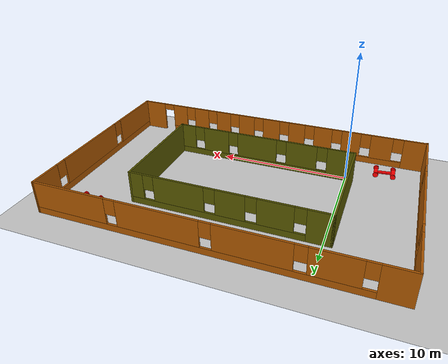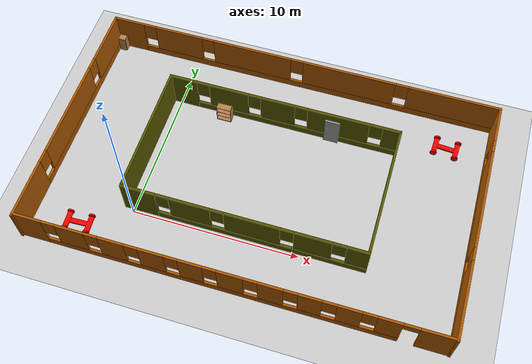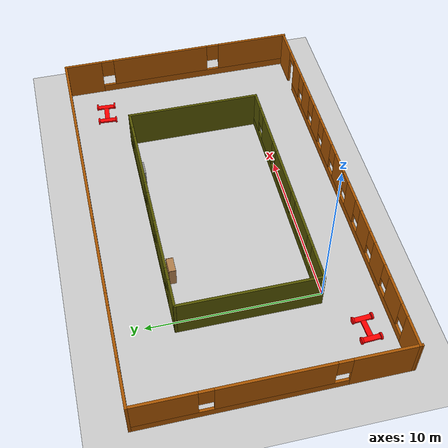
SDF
<sdf version="1.6">
 <world name="default">
  <plugin name="welcome" filename="libwelcome.so"/>
  <light name="sun" type="directional">
   <pose>0 0 10 0 -0 0</pose>
   <diffuse>0.8 0.8 0.8 1</diffuse>
   <specular>0.2 0.2 0.2 1</specular>
   <attenuation>
    <range>1000</range>
    <constant>0.9</constant>
    <linear>0.01</linear>
    <quadratic>0.001</quadratic>
   </attenuation>
   <direction>-0.5 0.1 -0.9</direction>
  </light>
  <model name="ground_plane">
   <static>1</static>
   <link name="link">
    <collision name="collision">
     <geometry><plane><normal>0 0 1</normal><size>100 100</size></plane></geometry>
     <surface><friction><ode><mu>100</mu><mu2>50</mu2></ode></friction></surface>
    </collision>
    <visual name="visual">
     <cast_shadows>0</cast_shadows>
     <geometry><plane><normal>0 0 1</normal><size>100 100</size></plane></geometry>
     <material>
      <script><uri>file://media/materials/scripts/gazebo.material</uri><name>Gazebo/Grey</name></script>
     </material>
    </visual>
   </link>
  </model>
  <gravity>0 0 -9.8</gravity>
  <magnetic_field>6e-06 2.3e-05 -4.2e-05</magnetic_field>
  <atmosphere type="adiabatic"/>
  <physics name="default_physics" default="0" type="ode">
   <max_step_size>0.001</max_step_size>
   <real_time_factor>1</real_time_factor>
   <real_time_update_rate>1000</real_time_update_rate>
  </physics>
  <scene><ambient>0.4 0.4 0.4 1</ambient><background>0.7 0.7 0.7 1</background><shadows>1</shadows></scene>
  <spherical_coordinates>
   <surface_model>EARTH_WGS84</surface_model>
   <latitude_deg>0</latitude_deg>
   <longitude_deg>0</longitude_deg>
   <elevation>0</elevation>
   <heading_deg>0</heading_deg>
  </spherical_coordinates>
  <model name="Building">
   <pose>6.81216 4.24314 0 0 -0 0</pose>
   <link name="Door_1">
    <collision name="Door_1_Collision">
     <geometry><box><size>0.9 0.17 2</size></box></geometry>
     <pose>0 0 1 0 -0 0</pose>
    </collision>
    <visual name="Door_1_Visual">
     <pose>0 0 1 0 -0 0</pose>
     <geometry><box><size>0.9 0.17 2</size></box></geometry>
     <material>
      <script><uri>file://media/materials/scripts/gazebo.material</uri><name>Gazebo/Grey</name></script>
     </material>
    </visual>
    <pose>2.94986 3.99433 0 0 -0 0</pose>
   </link>
   <link name="Wall_0">
    <pose>0 -7.35763 0 0 -0 0.002401</pose>
    <visual name="Wall_0_Visual_0">
     <pose>-11.5578 0 1.25 0 -0 0</pose>
     <geometry><box><size>1.79475 0.15 2.5</size></box></geometry>
     <material>
      <script><uri>file://media/materials/scripts/gazebo.material</uri><name>Gazebo/Grey</name></script>
      <ambient>0.666667 0.333333 0 1</ambient>
     </material>
     <meta><layer>0</layer></meta>
    </visual>
    <collision name="Wall_0_Collision_0">
     <geometry><box><size>1.79475 0.15 2.5</size></box></geometry>
     <pose>-11.5578 0 1.25 0 -0 0</pose>
    </collision>
    <visual name="Wall_0_Visual_1">
     <pose>11.4641 0 1.25 0 -0 0</pose>
     <geometry><box><size>1.98215 0.15 2.5</size></box></geometry>
     <material>
      <script><uri>file://media/materials/scripts/gazebo.material</uri><name>Gazebo/Grey</name></script>
      <ambient>0.666667 0.333333 0 1</ambient>
     </material>
     <meta><layer>0</layer></meta>
    </visual>
    <collision name="Wall_0_Collision_1">
     <geometry><box><size>1.98215 0.15 2.5</size></box></geometry>
     <pose>11.4641 0 1.25 0 -0 0</pose>
    </collision>
    <visual name="Wall_0_Visual_2">
     <pose>-0.543697 0 0.25 0 -0 0</pose>
     <geometry><box><size>20.2334 0.15 0.5</size></box></geometry>
     <material>
      <script><uri>file://media/materials/scripts/gazebo.material</uri><name>Gazebo/Grey</name></script>
      <ambient>0.666667 0.333333 0 1</ambient>
     </material>
     <meta><layer>0</layer></meta>
    </visual>
    <collision name="Wall_0_Collision_2">
     <geometry><box><size>20.2334 0.15 0.5</size></box></geometry>
     <pose>-0.543697 0 0.25 0 -0 0</pose>
    </collision>
    <visual name="Wall_0_Visual_3">
     <pose>-9.00211 0 1.5 0 -0 0</pose>
     <geometry><box><size>1.71659 0.15 2</size></box></geometry>
     <material>
      <script><uri>file://media/materials/scripts/gazebo.material</uri><name>Gazebo/Grey</name></script>
      <ambient>0.666667 0.333333 0 1</ambient>
     </material>
     <meta><layer>0</layer></meta>
    </visual>
    <collision name="Wall_0_Collision_3">
     <geometry><box><size>1.71659 0.15 2</size></box></geometry>
     <pose>-9.00211 0 1.5 0 -0 0</pose>
    </collision>
    <visual name="Wall_0_Visual_4">
     <pose>-6.57805 0 1.5 0 -0 0</pose>
     <geometry><box><size>1.53154 0.15 2</size></box></geometry>
     <material>
      <script><uri>file://media/materials/scripts/gazebo.material</uri><name>Gazebo/Grey</name></script>
      <ambient>0.666667 0.333333 0 1</ambient>
     </material>
     <meta><layer>0</layer></meta>
    </visual>
    <collision name="Wall_0_Collision_4">
     <geometry><box><size>1.53154 0.15 2</size></box></geometry>
     <pose>-6.57805 0 1.5 0 -0 0</pose>
    </collision>
    <visual name="Wall_0_Visual_5">
     <pose>-4.26501 0 1.5 0 -0 0</pose>
     <geometry><box><size>1.49454 0.15 2</size></box></geometry>
     <material>
      <script><uri>file://media/materials/scripts/gazebo.material</uri><name>Gazebo/Grey</name></script>
      <ambient>0.666667 0.333333 0 1</ambient>
     </material>
     <meta><layer>0</layer></meta>
    </visual>
    <collision name="Wall_0_Collision_5">
     <geometry><box><size>1.49454 0.15 2</size></box></geometry>
     <pose>-4.26501 0 1.5 0 -0 0</pose>
    </collision>
    <visual name="Wall_0_Visual_6">
     <pose>-2.02311 0 1.5 0 -0 0</pose>
     <geometry><box><size>1.38925 0.15 2</size></box></geometry>
     <material>
      <script><uri>file://media/materials/scripts/gazebo.material</uri><name>Gazebo/Grey</name></script>
      <ambient>0.666667 0.333333 0 1</ambient>
     </material>
     <meta><layer>0</layer></meta>
    </visual>
    <collision name="Wall_0_Collision_6">
     <geometry><box><size>1.38925 0.15 2</size></box></geometry>
     <pose>-2.02311 0 1.5 0 -0 0</pose>
    </collision>
    <visual name="Wall_0_Visual_7">
     <pose>0.21591 0 1.5 0 -0 0</pose>
     <geometry><box><size>1.48879 0.15 2</size></box></geometry>
     <material>
      <script><uri>file://media/materials/scripts/gazebo.material</uri><name>Gazebo/Grey</name></script>
      <ambient>0.666667 0.333333 0 1</ambient>
     </material>
     <meta><layer>0</layer></meta>
    </visual>
    <collision name="Wall_0_Collision_7">
     <geometry><box><size>1.48879 0.15 2</size></box></geometry>
     <pose>0.21591 0 1.5 0 -0 0</pose>
    </collision>
    <visual name="Wall_0_Visual_8">
     <pose>2.47057 0 1.5 0 -0 0</pose>
     <geometry><box><size>1.42052 0.15 2</size></box></geometry>
     <material>
      <script><uri>file://media/materials/scripts/gazebo.material</uri><name>Gazebo/Grey</name></script>
      <ambient>0.666667 0.333333 0 1</ambient>
     </material>
     <meta><layer>0</layer></meta>
    </visual>
    <collision name="Wall_0_Collision_8">
     <geometry><box><size>1.42052 0.15 2</size></box></geometry>
     <pose>2.47057 0 1.5 0 -0 0</pose>
    </collision>
    <visual name="Wall_0_Visual_9">
     <pose>4.63557 0 1.5 0 -0 0</pose>
     <geometry><box><size>1.30949 0.15 2</size></box></geometry>
     <material>
      <script><uri>file://media/materials/scripts/gazebo.material</uri><name>Gazebo/Grey</name></script>
      <ambient>0.666667 0.333333 0 1</ambient>
     </material>
     <meta><layer>0</layer></meta>
    </visual>
    <collision name="Wall_0_Collision_9">
     <geometry><box><size>1.30949 0.15 2</size></box></geometry>
     <pose>4.63557 0 1.5 0 -0 0</pose>
    </collision>
    <visual name="Wall_0_Visual_10">
     <pose>6.76357 0 1.5 0 -0 0</pose>
     <geometry><box><size>1.3465 0.15 2</size></box></geometry>
     <material>
      <script><uri>file://media/materials/scripts/gazebo.material</uri><name>Gazebo/Grey</name></script>
      <ambient>0.666667 0.333333 0 1</ambient>
     </material>
     <meta><layer>0</layer></meta>
    </visual>
    <collision name="Wall_0_Collision_10">
     <geometry><box><size>1.3465 0.15 2</size></box></geometry>
     <pose>6.76357 0 1.5 0 -0 0</pose>
    </collision>
    <visual name="Wall_0_Visual_11">
     <pose>8.90492 0 1.5 0 -0 0</pose>
     <geometry><box><size>1.33619 0.15 2</size></box></geometry>
     <material>
      <script><uri>file://media/materials/scripts/gazebo.material</uri><name>Gazebo/Grey</name></script>
      <ambient>0.666667 0.333333 0 1</ambient>
     </material>
     <meta><layer>0</layer></meta>
    </visual>
    <collision name="Wall_0_Collision_11">
     <geometry><box><size>1.33619 0.15 2</size></box></geometry>
     <pose>8.90492 0 1.5 0 -0 0</pose>
    </collision>
    <visual name="Wall_0_Visual_12">
     <pose>-10.2604 0 1.9 0 -0 0</pose>
     <geometry><box><size>0.8 0.15 1.2</size></box></geometry>
     <material>
      <script><uri>file://media/materials/scripts/gazebo.material</uri><name>Gazebo/Grey</name></script>
      <ambient>0.666667 0.333333 0 1</ambient>
     </material>
     <meta><layer>0</layer></meta>
    </visual>
    <collision name="Wall_0_Collision_12">
     <geometry><box><size>0.8 0.15 1.2</size></box></geometry>
     <pose>-10.2604 0 1.9 0 -0 0</pose>
    </collision>
    <visual name="Wall_0_Visual_13">
     <pose>-7.74382 0 1.9 0 -0 0</pose>
     <geometry><box><size>0.8 0.15 1.2</size></box></geometry>
     <material>
      <script><uri>file://media/materials/scripts/gazebo.material</uri><name>Gazebo/Grey</name></script>
      <ambient>0.666667 0.333333 0 1</ambient>
     </material>
     <meta><layer>0</layer></meta>
    </visual>
    <collision name="Wall_0_Collision_13">
     <geometry><box><size>0.8 0.15 1.2</size></box></geometry>
     <pose>-7.74382 0 1.9 0 -0 0</pose>
    </collision>
    <visual name="Wall_0_Visual_14">
     <pose>-5.41228 0 1.9 0 -0 0</pose>
     <geometry><box><size>0.8 0.15 1.2</size></box></geometry>
     <material>
      <script><uri>file://media/materials/scripts/gazebo.material</uri><name>Gazebo/Grey</name></script>
      <ambient>0.666667 0.333333 0 1</ambient>
     </material>
     <meta><layer>0</layer></meta>
    </visual>
    <collision name="Wall_0_Collision_14">
     <geometry><box><size>0.8 0.15 1.2</size></box></geometry>
     <pose>-5.41228 0 1.9 0 -0 0</pose>
    </collision>
    <visual name="Wall_0_Visual_15">
     <pose>-3.11774 0 1.9 0 -0 0</pose>
     <geometry><box><size>0.8 0.15 1.2</size></box></geometry>
     <material>
      <script><uri>file://media/materials/scripts/gazebo.material</uri><name>Gazebo/Grey</name></script>
      <ambient>0.666667 0.333333 0 1</ambient>
     </material>
     <meta><layer>0</layer></meta>
    </visual>
    <collision name="Wall_0_Collision_15">
     <geometry><box><size>0.8 0.15 1.2</size></box></geometry>
     <pose>-3.11774 0 1.9 0 -0 0</pose>
    </collision>
    <visual name="Wall_0_Visual_16">
     <pose>-0.928486 0 1.9 0 -0 0</pose>
     <geometry><box><size>0.8 0.15 1.2</size></box></geometry>
     <material>
      <script><uri>file://media/materials/scripts/gazebo.material</uri><name>Gazebo/Grey</name></script>
      <ambient>0.666667 0.333333 0 1</ambient>
     </material>
     <meta><layer>0</layer></meta>
    </visual>
    <collision name="Wall_0_Collision_16">
     <geometry><box><size>0.8 0.15 1.2</size></box></geometry>
     <pose>-0.928486 0 1.9 0 -0 0</pose>
    </collision>
    <visual name="Wall_0_Visual_17">
     <pose>1.36031 0 1.9 0 -0 0</pose>
     <geometry><box><size>0.8 0.15 1.2</size></box></geometry>
     <material>
      <script><uri>file://media/materials/scripts/gazebo.material</uri><name>Gazebo/Grey</name></script>
      <ambient>0.666667 0.333333 0 1</ambient>
     </material>
     <meta><layer>0</layer></meta>
    </visual>
    <collision name="Wall_0_Collision_17">
     <geometry><box><size>0.8 0.15 1.2</size></box></geometry>
     <pose>1.36031 0 1.9 0 -0 0</pose>
    </collision>
    <visual name="Wall_0_Visual_18">
     <pose>3.58083 0 1.9 0 -0 0</pose>
     <geometry><box><size>0.8 0.15 1.2</size></box></geometry>
     <material>
      <script><uri>file://media/materials/scripts/gazebo.material</uri><name>Gazebo/Grey</name></script>
      <ambient>0.666667 0.333333 0 1</ambient>
     </material>
     <meta><layer>0</layer></meta>
    </visual>
    <collision name="Wall_0_Collision_18">
     <geometry><box><size>0.8 0.15 1.2</size></box></geometry>
     <pose>3.58083 0 1.9 0 -0 0</pose>
    </collision>
    <visual name="Wall_0_Visual_19">
     <pose>5.69032 0 1.9 0 -0 0</pose>
     <geometry><box><size>0.8 0.15 1.2</size></box></geometry>
     <material>
      <script><uri>file://media/materials/scripts/gazebo.material</uri><name>Gazebo/Grey</name></script>
      <ambient>0.666667 0.333333 0 1</ambient>
     </material>
     <meta><layer>0</layer></meta>
    </visual>
    <collision name="Wall_0_Collision_19">
     <geometry><box><size>0.8 0.15 1.2</size></box></geometry>
     <pose>5.69032 0 1.9 0 -0 0</pose>
    </collision>
    <visual name="Wall_0_Visual_20">
     <pose>7.83682 0 1.9 0 -0 0</pose>
     <geometry><box><size>0.8 0.15 1.2</size></box></geometry>
     <material>
      <script><uri>file://media/materials/scripts/gazebo.material</uri><name>Gazebo/Grey</name></script>
      <ambient>0.666667 0.333333 0 1</ambient>
     </material>
     <meta><layer>0</layer></meta>
    </visual>
    <collision name="Wall_0_Collision_20">
     <geometry><box><size>0.8 0.15 1.2</size></box></geometry>
     <pose>7.83682 0 1.9 0 -0 0</pose>
    </collision>
    <visual name="Wall_0_Visual_21">
     <pose>10.023 0 2.25 0 -0 0</pose>
     <geometry><box><size>0.9 0.15 0.5</size></box></geometry>
     <material>
      <script><uri>file://media/materials/scripts/gazebo.material</uri><name>Gazebo/Grey</name></script>
      <ambient>0.666667 0.333333 0 1</ambient>
     </material>
     <meta><layer>0</layer></meta>
    </visual>
    <collision name="Wall_0_Collision_21">
     <geometry><box><size>0.9 0.15 0.5</size></box></geometry>
     <pose>10.023 0 2.25 0 -0 0</pose>
    </collision>
   </link>
   <link name="Wall_12">
    <collision name="Wall_12_Collision">
     <geometry><box><size>8.25 0.15 2.5</size></box></geometry>
     <pose>0 0 1.25 0 -0 0</pose>
    </collision>
    <visual name="Wall_12_Visual">
     <pose>0 0 1.25 0 -0 0</pose>
     <geometry><box><size>8.25 0.15 2.5</size></box></geometry>
     <material>
      <script><uri>file://media/materials/scripts/gazebo.material</uri><name>Gazebo/Grey</name></script>
      <ambient>0.333333 0.333333 0 1</ambient>
     </material>
     <meta><layer>0</layer></meta>
    </visual>
    <pose>-7.34158 0.069621 0 0 0 -1.5708</pose>
   </link>
   <link name="Wall_17">
    <pose>-0.166583 -3.98038 0 0 -0 0</pose>
    <visual name="Wall_17_Visual_0">
     <pose>-6.19156 0 1.25 0 -0 0</pose>
     <geometry><box><size>2.11688 0.15 2.5</size></box></geometry>
     <material>
      <script><uri>file://media/materials/scripts/gazebo.material</uri><name>Gazebo/Grey</name></script>
      <ambient>0.333333 0.333333 0 1</ambient>
     </material>
     <meta><layer>0</layer></meta>
    </visual>
    <collision name="Wall_17_Collision_0">
     <geometry><box><size>2.11688 0.15 2.5</size></box></geometry>
     <pose>-6.19156 0 1.25 0 -0 0</pose>
    </collision>
    <visual name="Wall_17_Visual_1">
     <pose>1.05844 0 0.25 0 -0 0</pose>
     <geometry><box><size>12.3831 0.15 0.5</size></box></geometry>
     <material>
      <script><uri>file://media/materials/scripts/gazebo.material</uri><name>Gazebo/Grey</name></script>
      <ambient>0.333333 0.333333 0 1</ambient>
     </material>
     <meta><layer>0</layer></meta>
    </visual>
    <collision name="Wall_17_Collision_1">
     <geometry><box><size>12.3831 0.15 0.5</size></box></geometry>
     <pose>1.05844 0 0.25 0 -0 0</pose>
    </collision>
    <visual name="Wall_17_Visual_2">
     <pose>-3.10907 0 1.5 0 -0 0</pose>
     <geometry><box><size>2.4481 0.15 2</size></box></geometry>
     <material>
      <script><uri>file://media/materials/scripts/gazebo.material</uri><name>Gazebo/Grey</name></script>
      <ambient>0.333333 0.333333 0 1</ambient>
     </material>
     <meta><layer>0</layer></meta>
    </visual>
    <collision name="Wall_17_Collision_2">
     <geometry><box><size>2.4481 0.15 2</size></box></geometry>
     <pose>-3.10907 0 1.5 0 -0 0</pose>
    </collision>
    <visual name="Wall_17_Visual_3">
     <pose>0.545036 0 1.5 0 -0 0</pose>
     <geometry><box><size>3.26012 0.15 2</size></box></geometry>
     <material>
      <script><uri>file://media/materials/scripts/gazebo.material</uri><name>Gazebo/Grey</name></script>
      <ambient>0.333333 0.333333 0 1</ambient>
     </material>
     <meta><layer>0</layer></meta>
    </visual>
    <collision name="Wall_17_Collision_3">
     <geometry><box><size>3.26012 0.15 2</size></box></geometry>
     <pose>0.545036 0 1.5 0 -0 0</pose>
    </collision>
    <visual name="Wall_17_Visual_4">
     <pose>4.05839 0 1.5 0 -0 0</pose>
     <geometry><box><size>2.1666 0.15 2</size></box></geometry>
     <material>
      <script><uri>file://media/materials/scripts/gazebo.material</uri><name>Gazebo/Grey</name></script>
      <ambient>0.333333 0.333333 0 1</ambient>
     </material>
     <meta><layer>0</layer></meta>
    </visual>
    <collision name="Wall_17_Collision_4">
     <geometry><box><size>2.1666 0.15 2</size></box></geometry>
     <pose>4.05839 0 1.5 0 -0 0</pose>
    </collision>
    <visual name="Wall_17_Visual_5">
     <pose>6.59585 0 1.5 0 -0 0</pose>
     <geometry><box><size>1.30831 0.15 2</size></box></geometry>
     <material>
      <script><uri>file://media/materials/scripts/gazebo.material</uri><name>Gazebo/Grey</name></script>
      <ambient>0.333333 0.333333 0 1</ambient>
     </material>
     <meta><layer>0</layer></meta>
    </visual>
    <collision name="Wall_17_Collision_5">
     <geometry><box><size>1.30831 0.15 2</size></box></geometry>
     <pose>6.59585 0 1.5 0 -0 0</pose>
    </collision>
    <visual name="Wall_17_Visual_6">
     <pose>-4.73312 0 1.9 0 -0 0</pose>
     <geometry><box><size>0.8 0.15 1.2</size></box></geometry>
     <material>
      <script><uri>file://media/materials/scripts/gazebo.material</uri><name>Gazebo/Grey</name></script>
      <ambient>0.333333 0.333333 0 1</ambient>
     </material>
     <meta><layer>0</layer></meta>
    </visual>
    <collision name="Wall_17_Collision_6">
     <geometry><box><size>0.8 0.15 1.2</size></box></geometry>
     <pose>-4.73312 0 1.9 0 -0 0</pose>
    </collision>
    <visual name="Wall_17_Visual_7">
     <pose>-1.48502 0 1.9 0 -0 0</pose>
     <geometry><box><size>0.8 0.15 1.2</size></box></geometry>
     <material>
      <script><uri>file://media/materials/scripts/gazebo.material</uri><name>Gazebo/Grey</name></script>
      <ambient>0.333333 0.333333 0 1</ambient>
     </material>
     <meta><layer>0</layer></meta>
    </visual>
    <collision name="Wall_17_Collision_7">
     <geometry><box><size>0.8 0.15 1.2</size></box></geometry>
     <pose>-1.48502 0 1.9 0 -0 0</pose>
    </collision>
    <visual name="Wall_17_Visual_8">
     <pose>2.5751 0 1.9 0 -0 0</pose>
     <geometry><box><size>0.8 0.15 1.2</size></box></geometry>
     <material>
      <script><uri>file://media/materials/scripts/gazebo.material</uri><name>Gazebo/Grey</name></script>
      <ambient>0.333333 0.333333 0 1</ambient>
     </material>
     <meta><layer>0</layer></meta>
    </visual>
    <collision name="Wall_17_Collision_8">
     <geometry><box><size>0.8 0.15 1.2</size></box></geometry>
     <pose>2.5751 0 1.9 0 -0 0</pose>
    </collision>
    <visual name="Wall_17_Visual_9">
     <pose>5.54169 0 1.9 0 -0 0</pose>
     <geometry><box><size>0.8 0.15 1.2</size></box></geometry>
     <material>
      <script><uri>file://media/materials/scripts/gazebo.material</uri><name>Gazebo/Grey</name></script>
      <ambient>0.333333 0.333333 0 1</ambient>
     </material>
     <meta><layer>0</layer></meta>
    </visual>
    <collision name="Wall_17_Collision_9">
     <geometry><box><size>0.8 0.15 1.2</size></box></geometry>
     <pose>5.54169 0 1.9 0 -0 0</pose>
    </collision>
   </link>
   <link name="Wall_18">
    <collision name="Wall_18_Collision">
     <geometry><box><size>8.25 0.15 2.5</size></box></geometry>
     <pose>0 0 1.25 0 -0 0</pose>
    </collision>
    <visual name="Wall_18_Visual">
     <pose>0 0 1.25 0 -0 0</pose>
     <geometry><box><size>8.25 0.15 2.5</size></box></geometry>
     <material>
      <script><uri>file://media/materials/scripts/gazebo.material</uri><name>Gazebo/Grey</name></script>
      <ambient>0.333333 0.333333 0 1</ambient>
     </material>
     <meta><layer>0</layer></meta>
    </visual>
    <pose>7.00842 0.069621 0 0 -0 1.5708</pose>
   </link>
   <link name="Wall_20">
    <pose>-0.166583 4.11962 0 0 -0 0</pose>
    <visual name="Wall_20_Visual_0">
     <pose>-6.37201 0 1.25 0 -0 0</pose>
     <geometry><box><size>1.75598 0.15 2.5</size></box></geometry>
     <material>
      <script><uri>file://media/materials/scripts/gazebo.material</uri><name>Gazebo/Grey</name></script>
      <ambient>0.333333 0.333333 0 1</ambient>
     </material>
     <meta><layer>0</layer></meta>
    </visual>
    <collision name="Wall_20_Collision_0">
     <geometry><box><size>1.75598 0.15 2.5</size></box></geometry>
     <pose>-6.37201 0 1.25 0 -0 0</pose>
    </collision>
    <visual name="Wall_20_Visual_1">
     <pose>0.87799 0 0.25 0 -0 0</pose>
     <geometry><box><size>12.744 0.15 0.5</size></box></geometry>
     <material>
      <script><uri>file://media/materials/scripts/gazebo.material</uri><name>Gazebo/Grey</name></script>
      <ambient>0.333333 0.333333 0 1</ambient>
     </material>
     <meta><layer>0</layer></meta>
    </visual>
    <collision name="Wall_20_Collision_1">
     <geometry><box><size>12.744 0.15 0.5</size></box></geometry>
     <pose>0.87799 0 0.25 0 -0 0</pose>
    </collision>
    <visual name="Wall_20_Visual_2">
     <pose>-3.44742 0 1.5 0 -0 0</pose>
     <geometry><box><size>2.49321 0.15 2</size></box></geometry>
     <material>
      <script><uri>file://media/materials/scripts/gazebo.material</uri><name>Gazebo/Grey</name></script>
      <ambient>0.333333 0.333333 0 1</ambient>
     </material>
     <meta><layer>0</layer></meta>
    </visual>
    <collision name="Wall_20_Collision_2">
     <geometry><box><size>2.49321 0.15 2</size></box></geometry>
     <pose>-3.44742 0 1.5 0 -0 0</pose>
    </collision>
    <visual name="Wall_20_Visual_3">
     <pose>-0.334657 0 1.5 0 -0 0</pose>
     <geometry><box><size>2.13231 0.15 2</size></box></geometry>
     <material>
      <script><uri>file://media/materials/scripts/gazebo.material</uri><name>Gazebo/Grey</name></script>
      <ambient>0.333333 0.333333 0 1</ambient>
     </material>
     <meta><layer>0</layer></meta>
    </visual>
    <collision name="Wall_20_Collision_3">
     <geometry><box><size>2.13231 0.15 2</size></box></geometry>
     <pose>-0.334657 0 1.5 0 -0 0</pose>
    </collision>
    <visual name="Wall_20_Visual_4">
     <pose>3.43223 0 1.5 0 -0 0</pose>
     <geometry><box><size>3.80147 0.15 2</size></box></geometry>
     <material>
      <script><uri>file://media/materials/scripts/gazebo.material</uri><name>Gazebo/Grey</name></script>
      <ambient>0.333333 0.333333 0 1</ambient>
     </material>
     <meta><layer>0</layer></meta>
    </visual>
    <collision name="Wall_20_Collision_4">
     <geometry><box><size>3.80147 0.15 2</size></box></geometry>
     <pose>3.43223 0 1.5 0 -0 0</pose>
    </collision>
    <visual name="Wall_20_Visual_5">
     <pose>6.69148 0 1.5 0 -0 0</pose>
     <geometry><box><size>1.11703 0.15 2</size></box></geometry>
     <material>
      <script><uri>file://media/materials/scripts/gazebo.material</uri><name>Gazebo/Grey</name></script>
      <ambient>0.333333 0.333333 0 1</ambient>
     </material>
     <meta><layer>0</layer></meta>
    </visual>
    <collision name="Wall_20_Collision_5">
     <geometry><box><size>1.11703 0.15 2</size></box></geometry>
     <pose>6.69148 0 1.5 0 -0 0</pose>
    </collision>
    <visual name="Wall_20_Visual_6">
     <pose>-5.09402 0 1.9 0 -0 0</pose>
     <geometry><box><size>0.8 0.15 1.2</size></box></geometry>
     <material>
      <script><uri>file://media/materials/scripts/gazebo.material</uri><name>Gazebo/Grey</name></script>
      <ambient>0.333333 0.333333 0 1</ambient>
     </material>
     <meta><layer>0</layer></meta>
    </visual>
    <collision name="Wall_20_Collision_6">
     <geometry><box><size>0.8 0.15 1.2</size></box></geometry>
     <pose>-5.09402 0 1.9 0 -0 0</pose>
    </collision>
    <visual name="Wall_20_Visual_7">
     <pose>-1.80081 0 1.9 0 -0 0</pose>
     <geometry><box><size>0.8 0.15 1.2</size></box></geometry>
     <material>
      <script><uri>file://media/materials/scripts/gazebo.material</uri><name>Gazebo/Grey</name></script>
      <ambient>0.333333 0.333333 0 1</ambient>
     </material>
     <meta><layer>0</layer></meta>
    </visual>
    <collision name="Wall_20_Collision_7">
     <geometry><box><size>0.8 0.15 1.2</size></box></geometry>
     <pose>-1.80081 0 1.9 0 -0 0</pose>
    </collision>
    <visual name="Wall_20_Visual_8">
     <pose>1.1315 0 1.9 0 -0 0</pose>
     <geometry><box><size>0.8 0.15 1.2</size></box></geometry>
     <material>
      <script><uri>file://media/materials/scripts/gazebo.material</uri><name>Gazebo/Grey</name></script>
      <ambient>0.333333 0.333333 0 1</ambient>
     </material>
     <meta><layer>0</layer></meta>
    </visual>
    <collision name="Wall_20_Collision_8">
     <geometry><box><size>0.8 0.15 1.2</size></box></geometry>
     <pose>1.1315 0 1.9 0 -0 0</pose>
    </collision>
    <visual name="Wall_20_Visual_9">
     <pose>5.73297 0 1.9 0 -0 0</pose>
     <geometry><box><size>0.8 0.15 1.2</size></box></geometry>
     <material>
      <script><uri>file://media/materials/scripts/gazebo.material</uri><name>Gazebo/Grey</name></script>
      <ambient>0.333333 0.333333 0 1</ambient>
     </material>
     <meta><layer>0</layer></meta>
    </visual>
    <collision name="Wall_20_Collision_9">
     <geometry><box><size>0.8 0.15 1.2</size></box></geometry>
     <pose>5.73297 0 1.9 0 -0 0</pose>
    </collision>
   </link>
   <link name="Wall_3">
    <pose>-12.3798 -0.052578 0 0 -0 1.5708</pose>
    <visual name="Wall_3_Visual_0">
     <pose>-5.67059 0 1.25 0 -0 0</pose>
     <geometry><box><size>3.65881 0.15 2.5</size></box></geometry>
     <material>
      <script><uri>file://media/materials/scripts/gazebo.material</uri><name>Gazebo/Grey</name></script>
      <ambient>0.666667 0.333333 0 1</ambient>
     </material>
     <meta><layer>0</layer></meta>
    </visual>
    <collision name="Wall_3_Collision_0">
     <geometry><box><size>3.65881 0.15 2.5</size></box></geometry>
     <pose>-5.67059 0 1.25 0 -0 0</pose>
    </collision>
    <visual name="Wall_3_Visual_1">
     <pose>1.8294 0 0.25 0 -0 0</pose>
     <geometry><box><size>11.3412 0.15 0.5</size></box></geometry>
     <material>
      <script><uri>file://media/materials/scripts/gazebo.material</uri><name>Gazebo/Grey</name></script>
      <ambient>0.666667 0.333333 0 1</ambient>
     </material>
     <meta><layer>0</layer></meta>
    </visual>
    <collision name="Wall_3_Collision_1">
     <geometry><box><size>11.3412 0.15 0.5</size></box></geometry>
     <pose>1.8294 0 0.25 0 -0 0</pose>
    </collision>
    <visual name="Wall_3_Visual_2">
     <pose>0.084691 0 1.5 0 -0 0</pose>
     <geometry><box><size>6.25176 0.15 2</size></box></geometry>
     <material>
      <script><uri>file://media/materials/scripts/gazebo.material</uri><name>Gazebo/Grey</name></script>
      <ambient>0.666667 0.333333 0 1</ambient>
     </material>
     <meta><layer>0</layer></meta>
    </visual>
    <collision name="Wall_3_Collision_2">
     <geometry><box><size>6.25176 0.15 2</size></box></geometry>
     <pose>0.084691 0 1.5 0 -0 0</pose>
    </collision>
    <visual name="Wall_3_Visual_3">
     <pose>5.75528 0 1.5 0 -0 0</pose>
     <geometry><box><size>3.48943 0.15 2</size></box></geometry>
     <material>
      <script><uri>file://media/materials/scripts/gazebo.material</uri><name>Gazebo/Grey</name></script>
      <ambient>0.666667 0.333333 0 1</ambient>
     </material>
     <meta><layer>0</layer></meta>
    </visual>
    <collision name="Wall_3_Collision_3">
     <geometry><box><size>3.48943 0.15 2</size></box></geometry>
     <pose>5.75528 0 1.5 0 -0 0</pose>
    </collision>
    <visual name="Wall_3_Visual_4">
     <pose>-3.44119 0 1.9 0 -0 0</pose>
     <geometry><box><size>0.8 0.15 1.2</size></box></geometry>
     <material>
      <script><uri>file://media/materials/scripts/gazebo.material</uri><name>Gazebo/Grey</name></script>
      <ambient>0.666667 0.333333 0 1</ambient>
     </material>
     <meta><layer>0</layer></meta>
    </visual>
    <collision name="Wall_3_Collision_4">
     <geometry><box><size>0.8 0.15 1.2</size></box></geometry>
     <pose>-3.44119 0 1.9 0 -0 0</pose>
    </collision>
    <visual name="Wall_3_Visual_5">
     <pose>3.61057 0 1.9 0 -0 0</pose>
     <geometry><box><size>0.8 0.15 1.2</size></box></geometry>
     <material>
      <script><uri>file://media/materials/scripts/gazebo.material</uri><name>Gazebo/Grey</name></script>
      <ambient>0.666667 0.333333 0 1</ambient>
     </material>
     <meta><layer>0</layer></meta>
    </visual>
    <collision name="Wall_3_Collision_5">
     <geometry><box><size>0.8 0.15 1.2</size></box></geometry>
     <pose>3.61057 0 1.9 0 -0 0</pose>
    </collision>
   </link>
   <link name="Wall_6">
    <pose>0.000109 7.47009 0 0 -0 0.000601</pose>
    <visual name="Wall_6_Visual_0">
     <pose>-11.4439 0 1.25 0 -0 0</pose>
     <geometry><box><size>2.02242 0.15 2.5</size></box></geometry>
     <material>
      <script><uri>file://media/materials/scripts/gazebo.material</uri><name>Gazebo/Grey</name></script>
      <ambient>0.666667 0.333333 0 1</ambient>
     </material>
     <meta><layer>0</layer></meta>
    </visual>
    <collision name="Wall_6_Collision_0">
     <geometry><box><size>2.02242 0.15 2.5</size></box></geometry>
     <pose>-11.4439 0 1.25 0 -0 0</pose>
    </collision>
    <visual name="Wall_6_Visual_1">
     <pose>1.01121 0 0.25 0 -0 0</pose>
     <geometry><box><size>22.8878 0.15 0.5</size></box></geometry>
     <material>
      <script><uri>file://media/materials/scripts/gazebo.material</uri><name>Gazebo/Grey</name></script>
      <ambient>0.666667 0.333333 0 1</ambient>
     </material>
     <meta><layer>0</layer></meta>
    </visual>
    <collision name="Wall_6_Collision_1">
     <geometry><box><size>22.8878 0.15 0.5</size></box></geometry>
     <pose>1.01121 0 0.25 0 -0 0</pose>
    </collision>
    <visual name="Wall_6_Visual_2">
     <pose>-8.07503 0 1.5 0 -0 0</pose>
     <geometry><box><size>3.11533 0.15 2</size></box></geometry>
     <material>
      <script><uri>file://media/materials/scripts/gazebo.material</uri><name>Gazebo/Grey</name></script>
      <ambient>0.666667 0.333333 0 1</ambient>
     </material>
     <meta><layer>0</layer></meta>
    </visual>
    <collision name="Wall_6_Collision_2">
     <geometry><box><size>3.11533 0.15 2</size></box></geometry>
     <pose>-8.07503 0 1.5 0 -0 0</pose>
    </collision>
    <visual name="Wall_6_Visual_3">
     <pose>-3.18084 0 1.5 0 -0 0</pose>
     <geometry><box><size>5.07304 0.15 2</size></box></geometry>
     <material>
      <script><uri>file://media/materials/scripts/gazebo.material</uri><name>Gazebo/Grey</name></script>
      <ambient>0.666667 0.333333 0 1</ambient>
     </material>
     <meta><layer>0</layer></meta>
    </visual>
    <collision name="Wall_6_Collision_3">
     <geometry><box><size>5.07304 0.15 2</size></box></geometry>
     <pose>-3.18084 0 1.5 0 -0 0</pose>
    </collision>
    <visual name="Wall_6_Visual_4">
     <pose>3.07789 0 1.5 0 -0 0</pose>
     <geometry><box><size>5.84443 0.15 2</size></box></geometry>
     <material>
      <script><uri>file://media/materials/scripts/gazebo.material</uri><name>Gazebo/Grey</name></script>
      <ambient>0.666667 0.333333 0 1</ambient>
     </material>
     <meta><layer>0</layer></meta>
    </visual>
    <collision name="Wall_6_Collision_4">
     <geometry><box><size>5.84443 0.15 2</size></box></geometry>
     <pose>3.07789 0 1.5 0 -0 0</pose>
    </collision>
    <visual name="Wall_6_Visual_5">
     <pose>9.62761 0 1.5 0 -0 0</pose>
     <geometry><box><size>5.65501 0.15 2</size></box></geometry>
     <material>
      <script><uri>file://media/materials/scripts/gazebo.material</uri><name>Gazebo/Grey</name></script>
      <ambient>0.666667 0.333333 0 1</ambient>
     </material>
     <meta><layer>0</layer></meta>
    </visual>
    <collision name="Wall_6_Collision_5">
     <geometry><box><size>5.65501 0.15 2</size></box></geometry>
     <pose>9.62761 0 1.5 0 -0 0</pose>
    </collision>
    <visual name="Wall_6_Visual_6">
     <pose>-10.0327 0 1.9 0 -0 0</pose>
     <geometry><box><size>0.8 0.15 1.2</size></box></geometry>
     <material>
      <script><uri>file://media/materials/scripts/gazebo.material</uri><name>Gazebo/Grey</name></script>
      <ambient>0.666667 0.333333 0 1</ambient>
     </material>
     <meta><layer>0</layer></meta>
    </visual>
    <collision name="Wall_6_Collision_6">
     <geometry><box><size>0.8 0.15 1.2</size></box></geometry>
     <pose>-10.0327 0 1.9 0 -0 0</pose>
    </collision>
    <visual name="Wall_6_Visual_7">
     <pose>-6.11736 0 1.9 0 -0 0</pose>
     <geometry><box><size>0.8 0.15 1.2</size></box></geometry>
     <material>
      <script><uri>file://media/materials/scripts/gazebo.material</uri><name>Gazebo/Grey</name></script>
      <ambient>0.666667 0.333333 0 1</ambient>
     </material>
     <meta><layer>0</layer></meta>
    </visual>
    <collision name="Wall_6_Collision_7">
     <geometry><box><size>0.8 0.15 1.2</size></box></geometry>
     <pose>-6.11736 0 1.9 0 -0 0</pose>
    </collision>
    <visual name="Wall_6_Visual_8">
     <pose>-0.244321 0 1.9 0 -0 0</pose>
     <geometry><box><size>0.8 0.15 1.2</size></box></geometry>
     <material>
      <script><uri>file://media/materials/scripts/gazebo.material</uri><name>Gazebo/Grey</name></script>
      <ambient>0.666667 0.333333 0 1</ambient>
     </material>
     <meta><layer>0</layer></meta>
    </visual>
    <collision name="Wall_6_Collision_8">
     <geometry><box><size>0.8 0.15 1.2</size></box></geometry>
     <pose>-0.244321 0 1.9 0 -0 0</pose>
    </collision>
    <visual name="Wall_6_Visual_9">
     <pose>6.40011 0 1.9 0 -0 0</pose>
     <geometry><box><size>0.8 0.15 1.2</size></box></geometry>
     <material>
      <script><uri>file://media/materials/scripts/gazebo.material</uri><name>Gazebo/Grey</name></script>
      <ambient>0.666667 0.333333 0 1</ambient>
     </material>
     <meta><layer>0</layer></meta>
    </visual>
    <collision name="Wall_6_Collision_9">
     <geometry><box><size>0.8 0.15 1.2</size></box></geometry>
     <pose>6.40011 0 1.9 0 -0 0</pose>
    </collision>
   </link>
   <link name="Wall_9">
    <pose>12.38 0.052534 0 0 0 -1.5708</pose>
    <visual name="Wall_9_Visual_0">
     <pose>-6.29597 0 1.25 0 -0 0</pose>
     <geometry><box><size>2.40805 0.15 2.5</size></box></geometry>
     <material>
      <script><uri>file://media/materials/scripts/gazebo.material</uri><name>Gazebo/Grey</name></script>
      <ambient>0.666667 0.333333 0 1</ambient>
     </material>
     <meta><layer>0</layer></meta>
    </visual>
    <collision name="Wall_9_Collision_0">
     <geometry><box><size>2.40805 0.15 2.5</size></box></geometry>
     <pose>-6.29597 0 1.25 0 -0 0</pose>
    </collision>
    <visual name="Wall_9_Visual_1">
     <pose>1.20403 0 0.25 0 -0 0</pose>
     <geometry><box><size>12.5919 0.15 0.5</size></box></geometry>
     <material>
      <script><uri>file://media/materials/scripts/gazebo.material</uri><name>Gazebo/Grey</name></script>
      <ambient>0.666667 0.333333 0 1</ambient>
     </material>
     <meta><layer>0</layer></meta>
    </visual>
    <collision name="Wall_9_Collision_1">
     <geometry><box><size>12.5919 0.15 0.5</size></box></geometry>
     <pose>1.20403 0 0.25 0 -0 0</pose>
    </collision>
    <visual name="Wall_9_Visual_2">
     <pose>-1.13249 0 1.5 0 -0 0</pose>
     <geometry><box><size>6.31892 0.15 2</size></box></geometry>
     <material>
      <script><uri>file://media/materials/scripts/gazebo.material</uri><name>Gazebo/Grey</name></script>
      <ambient>0.666667 0.333333 0 1</ambient>
     </material>
     <meta><layer>0</layer></meta>
    </visual>
    <collision name="Wall_9_Collision_2">
     <geometry><box><size>6.31892 0.15 2</size></box></geometry>
     <pose>-1.13249 0 1.5 0 -0 0</pose>
    </collision>
    <visual name="Wall_9_Visual_3">
     <pose>5.16349 0 1.5 0 -0 0</pose>
     <geometry><box><size>4.67303 0.15 2</size></box></geometry>
     <material>
      <script><uri>file://media/materials/scripts/gazebo.material</uri><name>Gazebo/Grey</name></script>
      <ambient>0.666667 0.333333 0 1</ambient>
     </material>
     <meta><layer>0</layer></meta>
    </visual>
    <collision name="Wall_9_Collision_3">
     <geometry><box><size>4.67303 0.15 2</size></box></geometry>
     <pose>5.16349 0 1.5 0 -0 0</pose>
    </collision>
    <visual name="Wall_9_Visual_4">
     <pose>-4.69195 0 1.9 0 -0 0</pose>
     <geometry><box><size>0.8 0.15 1.2</size></box></geometry>
     <material>
      <script><uri>file://media/materials/scripts/gazebo.material</uri><name>Gazebo/Grey</name></script>
      <ambient>0.666667 0.333333 0 1</ambient>
     </material>
     <meta><layer>0</layer></meta>
    </visual>
    <collision name="Wall_9_Collision_4">
     <geometry><box><size>0.8 0.15 1.2</size></box></geometry>
     <pose>-4.69195 0 1.9 0 -0 0</pose>
    </collision>
    <visual name="Wall_9_Visual_5">
     <pose>2.42697 0 1.9 0 -0 0</pose>
     <geometry><box><size>0.8 0.15 1.2</size></box></geometry>
     <material>
      <script><uri>file://media/materials/scripts/gazebo.material</uri><name>Gazebo/Grey</name></script>
      <ambient>0.666667 0.333333 0 1</ambient>
     </material>
     <meta><layer>0</layer></meta>
    </visual>
    <collision name="Wall_9_Collision_5">
     <geometry><box><size>0.8 0.15 1.2</size></box></geometry>
     <pose>2.42697 0 1.9 0 -0 0</pose>
    </collision>
   </link>
   <static>1</static>
  </model>
  <model name="bookshelf">
   <static>1</static>
   <link name="link">
    <inertial><mass>1</mass></inertial>
    <collision name="back">
     <pose>0 0.005 0.6 0 -0 0</pose>
     <geometry><box><size>0.9 0.01 1.2</size></box></geometry>
    </collision>
    <visual name="visual1">
     <pose>0 0.005 0.6 0 -0 0</pose>
     <geometry><box><size>0.9 0.01 1.2</size></box></geometry>
     <material>
      <script><uri>file://media/materials/scripts/gazebo.material</uri><name>Gazebo/Wood</name></script>
     </material>
    </visual>
    <collision name="left_side">
     <pose>0.45 -0.195 0.6 0 -0 0</pose>
     <geometry><box><size>0.02 0.4 1.2</size></box></geometry>
    </collision>
    <visual name="visual2">
     <pose>0.45 -0.195 0.6 0 -0 0</pose>
     <geometry><box><size>0.02 0.4 1.2</size></box></geometry>
     <material>
      <script><uri>file://media/materials/scripts/gazebo.material</uri><name>Gazebo/Wood</name></script>
     </material>
    </visual>
    <collision name="right_side">
     <pose>-0.45 -0.195 0.6 0 -0 0</pose>
     <geometry><box><size>0.02 0.4 1.2</size></box></geometry>
    </collision>
    <visual name="visual3">
     <pose>-0.45 -0.195 0.6 0 -0 0</pose>
     <geometry><box><size>0.02 0.4 1.2</size></box></geometry>
     <material>
      <script><uri>file://media/materials/scripts/gazebo.material</uri><name>Gazebo/Wood</name></script>
     </material>
    </visual>
    <collision name="bottom">
     <pose>0 -0.195 0.03 0 -0 0</pose>
     <geometry><box><size>0.88 0.4 0.06</size></box></geometry>
    </collision>
    <visual name="visual4">
     <pose>0 -0.195 0.03 0 -0 0</pose>
     <geometry><box><size>0.88 0.4 0.06</size></box></geometry>
     <material>
      <script><uri>file://media/materials/scripts/gazebo.material</uri><name>Gazebo/Wood</name></script>
     </material>
    </visual>
    <collision name="top">
     <pose>0 -0.195 1.19 0 -0 0</pose>
     <geometry><box><size>0.88 0.4 0.02</size></box></geometry>
    </collision>
    <visual name="visual5">
     <pose>0 -0.195 1.19 0 -0 0</pose>
     <geometry><box><size>0.88 0.4 0.02</size></box></geometry>
     <material>
      <script><uri>file://media/materials/scripts/gazebo.material</uri><name>Gazebo/Wood</name></script>
     </material>
    </visual>
    <collision name="low_shelf">
     <pose>0 -0.195 0.43 0 -0 0</pose>
     <geometry><box><size>0.88 0.4 0.02</size></box></geometry>
    </collision>
    <visual name="visual6">
     <pose>0 -0.195 0.43 0 -0 0</pose>
     <geometry><box><size>0.88 0.4 0.02</size></box></geometry>
     <material>
      <script><uri>file://media/materials/scripts/gazebo.material</uri><name>Gazebo/Wood</name></script>
     </material>
    </visual>
    <collision name="high_shelf">
     <pose>0 -0.195 0.8 0 -0 0</pose>
     <geometry><box><size>0.88 0.4 0.02</size></box></geometry>
    </collision>
    <visual name="visual7">
     <pose>0 -0.195 0.8 0 -0 0</pose>
     <geometry><box><size>0.88 0.4 0.02</size></box></geometry>
     <material>
      <script><uri>file://media/materials/scripts/gazebo.material</uri><name>Gazebo/Wood</name></script>
     </material>
    </visual>
   </link>
   <pose>2.99223 8.1082 0 0 -0 0</pose>
  </model>
  <model name="cabinet">
   <static>1</static>
   <link name="cabinet_bottom_plate">
    <inertial>
     <pose>0 0 -1 0 -0 0</pose>
     <inertia><ixx>2.05</ixx><ixy>0</ixy><ixz>0</ixz><iyy>2.05</iyy><iyz>0</iyz><izz>2.05</izz></inertia>
     <mass>25</mass>
    </inertial>
    <collision name="cabinet_bottom_plate_geom">
     <pose>0 0 0.01 0 -0 0</pose>
     <geometry><box><size>0.45 0.45 0.02</size></box></geometry>
    </collision>
    <visual name="cabinet_bottom_plate_geom_visual">
     <pose>0 0 0.01 0 -0 0</pose>
     <geometry><box><size>0.45 0.45 0.02</size></box></geometry>
     <material>
      <script><uri>file://media/materials/scripts/gazebo.material</uri><name>Gazebo/Wood</name></script>
     </material>
    </visual>
    <collision name="cabinet_bottom_plate_geom_cabinet_back_plate">
     <pose>0.235 0 0.51 0 -0 0</pose>
     <geometry><box><size>0.02 0.45 1.02</size></box></geometry>
    </collision>
    <visual name="cabinet_bottom_plate_geom_cabinet_back_plate_visual">
     <pose>0.235 0 0.51 0 -0 0</pose>
     <geometry><box><size>0.02 0.45 1.02</size></box></geometry>
     <material>
      <script><uri>file://media/materials/scripts/gazebo.material</uri><name>Gazebo/Wood</name></script>
     </material>
    </visual>
    <collision name="cabinet_bottom_plate_geom_cabinet_left_plate">
     <pose>0 0.235 0.51 0 -0 0</pose>
     <geometry><box><size>0.45 0.02 1.02</size></box></geometry>
    </collision>
    <visual name="cabinet_bottom_plate_geom_cabinet_left_plate_visual">
     <pose>0 0.235 0.51 0 -0 0</pose>
     <geometry><box><size>0.45 0.02 1.02</size></box></geometry>
     <material>
      <script><uri>file://media/materials/scripts/gazebo.material</uri><name>Gazebo/Wood</name></script>
     </material>
    </visual>
    <collision name="cabinet_bottom_plate_geom_cabinet_middle_plate">
     <pose>0 0 0.51 0 -0 0</pose>
     <geometry><box><size>0.45 0.45 0.02</size></box></geometry>
    </collision>
    <visual name="cabinet_bottom_plate_geom_cabinet_middle_plate_visual">
     <pose>0 0 0.51 0 -0 0</pose>
     <geometry><box><size>0.45 0.45 0.02</size></box></geometry>
     <material>
      <script><uri>file://media/materials/scripts/gazebo.material</uri><name>Gazebo/Wood</name></script>
     </material>
    </visual>
    <collision name="cabinet_bottom_plate_geom_cabinet_right_plate">
     <pose>0 -0.235 0.51 0 -0 0</pose>
     <geometry><box><size>0.45 0.02 1.02</size></box></geometry>
    </collision>
    <visual name="cabinet_bottom_plate_geom_cabinet_right_plate_visual">
     <pose>0 -0.235 0.51 0 -0 0</pose>
     <geometry><box><size>0.45 0.02 1.02</size></box></geometry>
     <material>
      <script><uri>file://media/materials/scripts/gazebo.material</uri><name>Gazebo/Wood</name></script>
     </material>
    </visual>
    <collision name="cabinet_bottom_plate_geom_cabinet_top_plate">
     <pose>0 0 1.01 0 -0 0</pose>
     <geometry><box><size>0.45 0.45 0.02</size></box></geometry>
    </collision>
    <visual name="cabinet_bottom_plate_geom_cabinet_top_plate_visual">
     <pose>0 0 1.01 0 -0 0</pose>
     <geometry><box><size>0.45 0.45 0.02</size></box></geometry>
     <material>
      <script><uri>file://media/materials/scripts/gazebo.material</uri><name>Gazebo/Wood</name></script>
     </material>
    </visual>
   </link>
   <pose>-5.23174 11.4449 0 0 -0 0</pose>
  </model>
  <model name="Robot">
   <link name="link_0">
    <pose>0.650121 -0 -0.012852 0 -0 0</pose>
    <inertial>
     <mass>1</mass>
     <inertia>
      <ixx>0.166667</ixx>
      <ixy>0</ixy>
      <ixz>0</ixz>
      <iyy>0.166667</iyy>
      <iyz>0</iyz>
      <izz>0.166667</izz>
     </inertia>
    </inertial>
    <visual name="visual">
     <geometry><box><size>0.3 1 0.1</size></box></geometry>
     <material>
      <lighting>1</lighting>
      <script><uri>file://media/materials/scripts/gazebo.material</uri><name>Gazebo/Grey</name></script>
      <shader type="pixel"><normal_map>__default__</normal_map></shader>
      <ambient>1 0 0 1</ambient>
      <diffuse>1 0 0 1</diffuse>
      <specular>0.01 0.01 0.01 1</specular>
      <emissive>0 0 0 1</emissive>
     </material>
    </visual>
    <collision name="collision">
     <geometry><box><size>0.3 1 0.1</size></box></geometry>
     <surface>
      <friction>
       <ode><mu>1</mu><mu2>1</mu2><fdir1>0 0 0</fdir1><slip1>0</slip1><slip2>0</slip2></ode>
       <torsional>
        <coefficient>1</coefficient>
        <patch_radius>0</patch_radius>
        <surface_radius>0</surface_radius>
        <use_patch_radius>1</use_patch_radius>
        <ode><slip>0</slip></ode>
       </torsional>
      </friction>
      <bounce><restitution_coefficient>0</restitution_coefficient><threshold>1e+06</threshold></bounce>
      <contact>
       <collide_without_contact>0</collide_without_contact>
       <collide_without_contact_bitmask>1</collide_without_contact_bitmask>
       <collide_bitmask>1</collide_bitmask>
       <ode>
        <soft_cfm>0</soft_cfm>
        <soft_erp>0.2</soft_erp>
        <kp>1e+13</kp>
        <kd>1</kd>
        <max_vel>0.01</max_vel>
        <min_depth>0</min_depth>
       </ode>
       <bullet>
        <split_impulse>1</split_impulse>
        <split_impulse_penetration_threshold>-0.01</split_impulse_penetration_threshold>
        <soft_cfm>0</soft_cfm>
        <soft_erp>0.2</soft_erp>
        <kp>1e+13</kp>
        <kd>1</kd>
       </bullet>
      </contact>
     </surface>
    </collision>
   </link>
   <link name="link_0_clone">
    <pose>2e-06 -0 -0.012852 0 -0 1.57</pose>
    <inertial>
     <mass>1</mass>
     <inertia>
      <ixx>0.166667</ixx>
      <ixy>0</ixy>
      <ixz>0</ixz>
      <iyy>0.166667</iyy>
      <iyz>0</iyz>
      <izz>0.166667</izz>
     </inertia>
    </inertial>
    <visual name="visual">
     <geometry><box><size>0.3 1 0.1</size></box></geometry>
     <material>
      <lighting>1</lighting>
      <script><uri>file://media/materials/scripts/gazebo.material</uri><name>Gazebo/Grey</name></script>
      <shader type="pixel"><normal_map>__default__</normal_map></shader>
      <ambient>1 0 0 1</ambient>
      <diffuse>1 0 0 1</diffuse>
      <specular>0.01 0.01 0.01 1</specular>
      <emissive>0 0 0 1</emissive>
     </material>
    </visual>
    <collision name="collision">
     <geometry><box><size>0.3 1 0.1</size></box></geometry>
     <surface>
      <friction>
       <ode><mu>1</mu><mu2>1</mu2><fdir1>0 0 0</fdir1><slip1>0</slip1><slip2>0</slip2></ode>
       <torsional>
        <coefficient>1</coefficient>
        <patch_radius>0</patch_radius>
        <surface_radius>0</surface_radius>
        <use_patch_radius>1</use_patch_radius>
        <ode><slip>0</slip></ode>
       </torsional>
      </friction>
      <bounce><restitution_coefficient>0</restitution_coefficient><threshold>1e+06</threshold></bounce>
      <contact>
       <collide_without_contact>0</collide_without_contact>
       <collide_without_contact_bitmask>1</collide_without_contact_bitmask>
       <collide_bitmask>1</collide_bitmask>
       <ode>
        <soft_cfm>0</soft_cfm>
        <soft_erp>0.2</soft_erp>
        <kp>1e+13</kp>
        <kd>1</kd>
        <max_vel>0.01</max_vel>
        <min_depth>0</min_depth>
       </ode>
       <bullet>
        <split_impulse>1</split_impulse>
        <split_impulse_penetration_threshold>-0.01</split_impulse_penetration_threshold>
        <soft_cfm>0</soft_cfm>
        <soft_erp>0.2</soft_erp>
        <kp>1e+13</kp>
        <kd>1</kd>
       </bullet>
      </contact>
     </surface>
    </collision>
   </link>
   <link name="link_0_clone_0">
    <pose>-0.650118 0 -0.012852 0 -0 0</pose>
    <inertial>
     <mass>1</mass>
     <inertia>
      <ixx>0.166667</ixx>
      <ixy>0</ixy>
      <ixz>0</ixz>
      <iyy>0.166667</iyy>
      <iyz>0</iyz>
      <izz>0.166667</izz>
     </inertia>
    </inertial>
    <visual name="visual">
     <geometry><box><size>0.3 1 0.1</size></box></geometry>
     <material>
      <lighting>1</lighting>
      <script><uri>file://media/materials/scripts/gazebo.material</uri><name>Gazebo/Grey</name></script>
      <shader type="pixel"><normal_map>__default__</normal_map></shader>
      <ambient>1 0 0 1</ambient>
      <diffuse>1 0 0 1</diffuse>
      <specular>0.01 0.01 0.01 1</specular>
      <emissive>0 0 0 1</emissive>
     </material>
    </visual>
    <collision name="collision">
     <geometry><box><size>0.3 1 0.1</size></box></geometry>
     <surface>
      <friction>
       <ode><mu>1</mu><mu2>1</mu2><fdir1>0 0 0</fdir1><slip1>0</slip1><slip2>0</slip2></ode>
       <torsional>
        <coefficient>1</coefficient>
        <patch_radius>0</patch_radius>
        <surface_radius>0</surface_radius>
        <use_patch_radius>1</use_patch_radius>
        <ode><slip>0</slip></ode>
       </torsional>
      </friction>
      <bounce><restitution_coefficient>0</restitution_coefficient><threshold>1e+06</threshold></bounce>
      <contact>
       <collide_without_contact>0</collide_without_contact>
       <collide_without_contact_bitmask>1</collide_without_contact_bitmask>
       <collide_bitmask>1</collide_bitmask>
       <ode>
        <soft_cfm>0</soft_cfm>
        <soft_erp>0.2</soft_erp>
        <kp>1e+13</kp>
        <kd>1</kd>
        <max_vel>0.01</max_vel>
        <min_depth>0</min_depth>
       </ode>
       <bullet>
        <split_impulse>1</split_impulse>
        <split_impulse_penetration_threshold>-0.01</split_impulse_penetration_threshold>
        <soft_cfm>0</soft_cfm>
        <soft_erp>0.2</soft_erp>
        <kp>1e+13</kp>
        <kd>1</kd>
       </bullet>
      </contact>
     </surface>
    </collision>
   </link>
   <link name="link_2">
    <pose>0.650121 -0.550159 0.032112 1.57 -0 0</pose>
    <inertial>
     <mass>1</mass>
     <inertia><ixx>0.145833</ixx><ixy>0</ixy><ixz>0</ixz><iyy>0.145833</iyy><iyz>0</iyz><izz>0.125</izz></inertia>
    </inertial>
    <visual name="visual">
     <geometry><cylinder><radius>0.2</radius><length>0.1</length></cylinder></geometry>
     <material>
      <lighting>1</lighting>
      <script><uri>file://media/materials/scripts/gazebo.material</uri><name>Gazebo/Grey</name></script>
      <shader type="pixel"><normal_map>__default__</normal_map></shader>
      <ambient>1 0 0 1</ambient>
      <diffuse>1 0 0 1</diffuse>
      <specular>0.01 0.01 0.01 1</specular>
      <emissive>0 0 0 1</emissive>
     </material>
    </visual>
    <collision name="collision">
     <geometry><cylinder><radius>0.2</radius><length>0.1</length></cylinder></geometry>
     <surface>
      <friction>
       <ode><mu>1</mu><mu2>1</mu2><fdir1>0 0 0</fdir1><slip1>0</slip1><slip2>0</slip2></ode>
       <torsional>
        <coefficient>1</coefficient>
        <patch_radius>0</patch_radius>
        <surface_radius>0</surface_radius>
        <use_patch_radius>1</use_patch_radius>
        <ode><slip>0</slip></ode>
       </torsional>
      </friction>
      <bounce><restitution_coefficient>0</restitution_coefficient><threshold>1e+06</threshold></bounce>
      <contact>
       <collide_without_contact>0</collide_without_contact>
       <collide_without_contact_bitmask>1</collide_without_contact_bitmask>
       <collide_bitmask>1</collide_bitmask>
       <ode>
        <soft_cfm>0</soft_cfm>
        <soft_erp>0.2</soft_erp>
        <kp>1e+13</kp>
        <kd>1</kd>
        <max_vel>0.01</max_vel>
        <min_depth>0</min_depth>
       </ode>
       <bullet>
        <split_impulse>1</split_impulse>
        <split_impulse_penetration_threshold>-0.01</split_impulse_penetration_threshold>
        <soft_cfm>0</soft_cfm>
        <soft_erp>0.2</soft_erp>
        <kp>1e+13</kp>
        <kd>1</kd>
       </bullet>
      </contact>
     </surface>
    </collision>
   </link>
   <link name="link_2_clone">
    <pose>0.650121 0.550159 0.032148 1.57 -0 0</pose>
    <inertial>
     <mass>1</mass>
     <inertia><ixx>0.145833</ixx><ixy>0</ixy><ixz>0</ixz><iyy>0.145833</iyy><iyz>0</iyz><izz>0.125</izz></inertia>
    </inertial>
    <visual name="visual">
     <geometry><cylinder><radius>0.2</radius><length>0.1</length></cylinder></geometry>
     <material>
      <lighting>1</lighting>
      <script><uri>file://media/materials/scripts/gazebo.material</uri><name>Gazebo/Grey</name></script>
      <shader type="pixel"><normal_map>__default__</normal_map></shader>
      <ambient>1 0 0 1</ambient>
      <diffuse>1 0 0 1</diffuse>
      <specular>0.01 0.01 0.01 1</specular>
      <emissive>0 0 0 1</emissive>
     </material>
    </visual>
    <collision name="collision">
     <geometry><cylinder><radius>0.2</radius><length>0.1</length></cylinder></geometry>
     <surface>
      <friction>
       <ode><mu>1</mu><mu2>1</mu2><fdir1>0 0 0</fdir1><slip1>0</slip1><slip2>0</slip2></ode>
       <torsional>
        <coefficient>1</coefficient>
        <patch_radius>0</patch_radius>
        <surface_radius>0</surface_radius>
        <use_patch_radius>1</use_patch_radius>
        <ode><slip>0</slip></ode>
       </torsional>
      </friction>
      <bounce><restitution_coefficient>0</restitution_coefficient><threshold>1e+06</threshold></bounce>
      <contact>
       <collide_without_contact>0</collide_without_contact>
       <collide_without_contact_bitmask>1</collide_without_contact_bitmask>
       <collide_bitmask>1</collide_bitmask>
       <ode>
        <soft_cfm>0</soft_cfm>
        <soft_erp>0.2</soft_erp>
        <kp>1e+13</kp>
        <kd>1</kd>
        <max_vel>0.01</max_vel>
        <min_depth>0</min_depth>
       </ode>
       <bullet>
        <split_impulse>1</split_impulse>
        <split_impulse_penetration_threshold>-0.01</split_impulse_penetration_threshold>
        <soft_cfm>0</soft_cfm>
        <soft_erp>0.2</soft_erp>
        <kp>1e+13</kp>
        <kd>1</kd>
       </bullet>
      </contact>
     </surface>
    </collision>
   </link>
   <link name="link_2_clone_0">
    <pose>-0.650118 -0.550159 -0.012852 1.57 -0 0</pose>
    <inertial>
     <mass>1</mass>
     <inertia><ixx>0.145833</ixx><ixy>0</ixy><ixz>0</ixz><iyy>0.145833</iyy><iyz>0</iyz><izz>0.125</izz></inertia>
    </inertial>
    <visual name="visual">
     <geometry><cylinder><radius>0.2</radius><length>0.1</length></cylinder></geometry>
     <material>
      <lighting>1</lighting>
      <script><uri>file://media/materials/scripts/gazebo.material</uri><name>Gazebo/Grey</name></script>
      <shader type="pixel"><normal_map>__default__</normal_map></shader>
      <ambient>1 0 0 1</ambient>
      <diffuse>1 0 0 1</diffuse>
      <specular>0.01 0.01 0.01 1</specular>
      <emissive>0 0 0 1</emissive>
     </material>
    </visual>
    <collision name="collision">
     <geometry><cylinder><radius>0.2</radius><length>0.1</length></cylinder></geometry>
     <surface>
      <friction>
       <ode><mu>1</mu><mu2>1</mu2><fdir1>0 0 0</fdir1><slip1>0</slip1><slip2>0</slip2></ode>
       <torsional>
        <coefficient>1</coefficient>
        <patch_radius>0</patch_radius>
        <surface_radius>0</surface_radius>
        <use_patch_radius>1</use_patch_radius>
        <ode><slip>0</slip></ode>
       </torsional>
      </friction>
      <bounce><restitution_coefficient>0</restitution_coefficient><threshold>1e+06</threshold></bounce>
      <contact>
       <collide_without_contact>0</collide_without_contact>
       <collide_without_contact_bitmask>1</collide_without_contact_bitmask>
       <collide_bitmask>1</collide_bitmask>
       <ode>
        <soft_cfm>0</soft_cfm>
        <soft_erp>0.2</soft_erp>
        <kp>1e+13</kp>
        <kd>1</kd>
        <max_vel>0.01</max_vel>
        <min_depth>0</min_depth>
       </ode>
       <bullet>
        <split_impulse>1</split_impulse>
        <split_impulse_penetration_threshold>-0.01</split_impulse_penetration_threshold>
        <soft_cfm>0</soft_cfm>
        <soft_erp>0.2</soft_erp>
        <kp>1e+13</kp>
        <kd>1</kd>
       </bullet>
      </contact>
     </surface>
    </collision>
   </link>
   <link name="link_2_clone_1">
    <pose>-0.650118 0.550159 -0.012852 1.57 -0 0</pose>
    <inertial>
     <mass>1</mass>
     <inertia><ixx>0.145833</ixx><ixy>0</ixy><ixz>0</ixz><iyy>0.145833</iyy><iyz>0</iyz><izz>0.125</izz></inertia>
    </inertial>
    <visual name="visual">
     <geometry><cylinder><radius>0.2</radius><length>0.1</length></cylinder></geometry>
     <material>
      <lighting>1</lighting>
      <script><uri>file://media/materials/scripts/gazebo.material</uri><name>Gazebo/Grey</name></script>
      <shader type="pixel"><normal_map>__default__</normal_map></shader>
      <ambient>1 0 0 1</ambient>
      <diffuse>1 0 0 1</diffuse>
      <specular>0.01 0.01 0.01 1</specular>
      <emissive>0 0 0 1</emissive>
     </material>
    </visual>
    <collision name="collision">
     <geometry><cylinder><radius>0.2</radius><length>0.1</length></cylinder></geometry>
     <surface>
      <friction>
       <ode><mu>1</mu><mu2>1</mu2><fdir1>0 0 0</fdir1><slip1>0</slip1><slip2>0</slip2></ode>
       <torsional>
        <coefficient>1</coefficient>
        <patch_radius>0</patch_radius>
        <surface_radius>0</surface_radius>
        <use_patch_radius>1</use_patch_radius>
        <ode><slip>0</slip></ode>
       </torsional>
      </friction>
      <bounce><restitution_coefficient>0</restitution_coefficient><threshold>1e+06</threshold></bounce>
      <contact>
       <collide_without_contact>0</collide_without_contact>
       <collide_without_contact_bitmask>1</collide_without_contact_bitmask>
       <collide_bitmask>1</collide_bitmask>
       <ode>
        <soft_cfm>0</soft_cfm>
        <soft_erp>0.2</soft_erp>
        <kp>1e+13</kp>
        <kd>1</kd>
        <max_vel>0.01</max_vel>
        <min_depth>0</min_depth>
       </ode>
       <bullet>
        <split_impulse>1</split_impulse>
        <split_impulse_penetration_threshold>-0.01</split_impulse_penetration_threshold>
        <soft_cfm>0</soft_cfm>
        <soft_erp>0.2</soft_erp>
        <kp>1e+13</kp>
        <kd>1</kd>
       </bullet>
      </contact>
     </surface>
    </collision>
   </link>
   <joint name="link_0_JOINT_2" type="revolute">
    <parent>link_0</parent>
    <child>link_2</child>
    <axis>
     <xyz>1 0 0</xyz>
     <use_parent_model_frame>0</use_parent_model_frame>
     <limit>
      <lower>-1.79769e+308</lower>
      <upper>1.79769e+308</upper>
      <effort>-1</effort>
      <velocity>-1</velocity>
     </limit>
     <dynamics>
      <spring_reference>0</spring_reference>
      <spring_stiffness>0</spring_stiffness>
      <damping>0</damping>
      <friction>0</friction>
     </dynamics>
    </axis>
    <physics>
     <ode><limit><cfm>0</cfm><erp>0.2</erp></limit><suspension><cfm>0</cfm><erp>0.2</erp></suspension></ode>
    </physics>
   </joint>
   <joint name="link_0_JOINT_3" type="revolute">
    <parent>link_0</parent>
    <child>link_2_clone</child>
    <axis>
     <xyz>1 0 0</xyz>
     <use_parent_model_frame>0</use_parent_model_frame>
     <limit>
      <lower>-1.79769e+308</lower>
      <upper>1.79769e+308</upper>
      <effort>-1</effort>
      <velocity>-1</velocity>
     </limit>
     <dynamics>
      <spring_reference>0</spring_reference>
      <spring_stiffness>0</spring_stiffness>
      <damping>0</damping>
      <friction>0</friction>
     </dynamics>
    </axis>
    <physics>
     <ode><limit><cfm>0</cfm><erp>0.2</erp></limit><suspension><cfm>0</cfm><erp>0.2</erp></suspension></ode>
    </physics>
   </joint>
   <joint name="link_0_clone_0_JOINT_4" type="revolute">
    <parent>link_0_clone_0</parent>
    <child>link_2_clone_0</child>
    <axis>
     <xyz>1 0 0</xyz>
     <use_parent_model_frame>0</use_parent_model_frame>
     <limit>
      <lower>-1.79769e+308</lower>
      <upper>1.79769e+308</upper>
      <effort>-1</effort>
      <velocity>-1</velocity>
     </limit>
     <dynamics>
      <spring_reference>0</spring_reference>
      <spring_stiffness>0</spring_stiffness>
      <damping>0</damping>
      <friction>0</friction>
     </dynamics>
    </axis>
    <physics>
     <ode><limit><cfm>0</cfm><erp>0.2</erp></limit><suspension><cfm>0</cfm><erp>0.2</erp></suspension></ode>
    </physics>
   </joint>
   <joint name="link_0_clone_0_JOINT_5" type="revolute">
    <parent>link_0_clone_0</parent>
    <child>link_2_clone_1</child>
    <axis>
     <xyz>1 0 0</xyz>
     <use_parent_model_frame>0</use_parent_model_frame>
     <limit>
      <lower>-1.79769e+308</lower>
      <upper>1.79769e+308</upper>
      <effort>-1</effort>
      <velocity>-1</velocity>
     </limit>
     <dynamics>
      <spring_reference>0</spring_reference>
      <spring_stiffness>0</spring_stiffness>
      <damping>0</damping>
      <friction>0</friction>
     </dynamics>
    </axis>
    <physics>
     <ode><limit><cfm>0</cfm><erp>0.2</erp></limit><suspension><cfm>0</cfm><erp>0.2</erp></suspension></ode>
    </physics>
   </joint>
   <joint name="link_0_clone_JOINT_0" type="revolute">
    <parent>link_0_clone</parent>
    <child>link_0</child>
    <axis>
     <xyz>1 0 0</xyz>
     <use_parent_model_frame>0</use_parent_model_frame>
     <limit>
      <lower>-1.79769e+308</lower>
      <upper>1.79769e+308</upper>
      <effort>-1</effort>
      <velocity>-1</velocity>
     </limit>
     <dynamics>
      <spring_reference>0</spring_reference>
      <spring_stiffness>0</spring_stiffness>
      <damping>0</damping>
      <friction>0</friction>
     </dynamics>
    </axis>
    <physics>
     <ode><limit><cfm>0</cfm><erp>0.2</erp></limit><suspension><cfm>0</cfm><erp>0.2</erp></suspension></ode>
    </physics>
   </joint>
   <joint name="link_0_clone_JOINT_1" type="revolute">
    <parent>link_0_clone</parent>
    <child>link_0_clone_0</child>
    <axis>
     <xyz>1 0 0</xyz>
     <use_parent_model_frame>0</use_parent_model_frame>
     <limit>
      <lower>-1.79769e+308</lower>
      <upper>1.79769e+308</upper>
      <effort>-1</effort>
      <velocity>-1</velocity>
     </limit>
     <dynamics>
      <spring_reference>0</spring_reference>
      <spring_stiffness>0</spring_stiffness>
      <damping>0</damping>
      <friction>0</friction>
     </dynamics>
    </axis>
    <physics>
     <ode><limit><cfm>0</cfm><erp>0.2</erp></limit><suspension><cfm>0</cfm><erp>0.2</erp></suspension></ode>
    </physics>
   </joint>
   <static>0</static>
   <pose>-2.78681 -1.62245 0.190363 -2.6e-05 0.034581 0.053221</pose>
  </model>
  <model name="Robot_clone">
   <link name="link_0">
    <pose>0.650121 -0 -0.012852 0 -0 0</pose>
    <inertial>
     <mass>1</mass>
     <inertia>
      <ixx>0.166667</ixx>
      <ixy>0</ixy>
      <ixz>0</ixz>
      <iyy>0.166667</iyy>
      <iyz>0</iyz>
      <izz>0.166667</izz>
     </inertia>
    </inertial>
    <visual name="visual">
     <geometry><box><size>0.3 1 0.1</size></box></geometry>
     <material>
      <lighting>1</lighting>
      <script><uri>file://media/materials/scripts/gazebo.material</uri><name>Gazebo/Grey</name></script>
      <shader type="pixel"><normal_map>__default__</normal_map></shader>
      <ambient>1 0 0 1</ambient>
      <diffuse>1 0 0 1</diffuse>
      <specular>0.01 0.01 0.01 1</specular>
      <emissive>0 0 0 1</emissive>
     </material>
    </visual>
    <collision name="collision">
     <geometry><box><size>0.3 1 0.1</size></box></geometry>
     <surface>
      <friction>
       <ode><mu>1</mu><mu2>1</mu2><fdir1>0 0 0</fdir1><slip1>0</slip1><slip2>0</slip2></ode>
       <torsional>
        <coefficient>1</coefficient>
        <patch_radius>0</patch_radius>
        <surface_radius>0</surface_radius>
        <use_patch_radius>1</use_patch_radius>
        <ode><slip>0</slip></ode>
       </torsional>
      </friction>
      <bounce><restitution_coefficient>0</restitution_coefficient><threshold>1e+06</threshold></bounce>
      <contact>
       <collide_without_contact>0</collide_without_contact>
       <collide_without_contact_bitmask>1</collide_without_contact_bitmask>
       <collide_bitmask>1</collide_bitmask>
       <ode>
        <soft_cfm>0</soft_cfm>
        <soft_erp>0.2</soft_erp>
        <kp>1e+13</kp>
        <kd>1</kd>
        <max_vel>0.01</max_vel>
        <min_depth>0</min_depth>
       </ode>
       <bullet>
        <split_impulse>1</split_impulse>
        <split_impulse_penetration_threshold>-0.01</split_impulse_penetration_threshold>
        <soft_cfm>0</soft_cfm>
        <soft_erp>0.2</soft_erp>
        <kp>1e+13</kp>
        <kd>1</kd>
       </bullet>
      </contact>
     </surface>
    </collision>
   </link>
   <link name="link_0_clone">
    <pose>2e-06 -0 -0.012852 0 -0 1.57</pose>
    <inertial>
     <mass>1</mass>
     <inertia>
      <ixx>0.166667</ixx>
      <ixy>0</ixy>
      <ixz>0</ixz>
      <iyy>0.166667</iyy>
      <iyz>0</iyz>
      <izz>0.166667</izz>
     </inertia>
    </inertial>
    <visual name="visual">
     <geometry><box><size>0.3 1 0.1</size></box></geometry>
     <material>
      <lighting>1</lighting>
      <script><uri>file://media/materials/scripts/gazebo.material</uri><name>Gazebo/Grey</name></script>
      <shader type="pixel"><normal_map>__default__</normal_map></shader>
      <ambient>1 0 0 1</ambient>
      <diffuse>1 0 0 1</diffuse>
      <specular>0.01 0.01 0.01 1</specular>
      <emissive>0 0 0 1</emissive>
     </material>
    </visual>
    <collision name="collision">
     <geometry><box><size>0.3 1 0.1</size></box></geometry>
     <surface>
      <friction>
       <ode><mu>1</mu><mu2>1</mu2><fdir1>0 0 0</fdir1><slip1>0</slip1><slip2>0</slip2></ode>
       <torsional>
        <coefficient>1</coefficient>
        <patch_radius>0</patch_radius>
        <surface_radius>0</surface_radius>
        <use_patch_radius>1</use_patch_radius>
        <ode><slip>0</slip></ode>
       </torsional>
      </friction>
      <bounce><restitution_coefficient>0</restitution_coefficient><threshold>1e+06</threshold></bounce>
      <contact>
       <collide_without_contact>0</collide_without_contact>
       <collide_without_contact_bitmask>1</collide_without_contact_bitmask>
       <collide_bitmask>1</collide_bitmask>
       <ode>
        <soft_cfm>0</soft_cfm>
        <soft_erp>0.2</soft_erp>
        <kp>1e+13</kp>
        <kd>1</kd>
        <max_vel>0.01</max_vel>
        <min_depth>0</min_depth>
       </ode>
       <bullet>
        <split_impulse>1</split_impulse>
        <split_impulse_penetration_threshold>-0.01</split_impulse_penetration_threshold>
        <soft_cfm>0</soft_cfm>
        <soft_erp>0.2</soft_erp>
        <kp>1e+13</kp>
        <kd>1</kd>
       </bullet>
      </contact>
     </surface>
    </collision>
   </link>
   <link name="link_0_clone_0">
    <pose>-0.650118 0 -0.012852 0 -0 0</pose>
    <inertial>
     <mass>1</mass>
     <inertia>
      <ixx>0.166667</ixx>
      <ixy>0</ixy>
      <ixz>0</ixz>
      <iyy>0.166667</iyy>
      <iyz>0</iyz>
      <izz>0.166667</izz>
     </inertia>
    </inertial>
    <visual name="visual">
     <geometry><box><size>0.3 1 0.1</size></box></geometry>
     <material>
      <lighting>1</lighting>
      <script><uri>file://media/materials/scripts/gazebo.material</uri><name>Gazebo/Grey</name></script>
      <shader type="pixel"><normal_map>__default__</normal_map></shader>
      <ambient>1 0 0 1</ambient>
      <diffuse>1 0 0 1</diffuse>
      <specular>0.01 0.01 0.01 1</specular>
      <emissive>0 0 0 1</emissive>
     </material>
    </visual>
    <collision name="collision">
     <geometry><box><size>0.3 1 0.1</size></box></geometry>
     <surface>
      <friction>
       <ode><mu>1</mu><mu2>1</mu2><fdir1>0 0 0</fdir1><slip1>0</slip1><slip2>0</slip2></ode>
       <torsional>
        <coefficient>1</coefficient>
        <patch_radius>0</patch_radius>
        <surface_radius>0</surface_radius>
        <use_patch_radius>1</use_patch_radius>
        <ode><slip>0</slip></ode>
       </torsional>
      </friction>
      <bounce><restitution_coefficient>0</restitution_coefficient><threshold>1e+06</threshold></bounce>
      <contact>
       <collide_without_contact>0</collide_without_contact>
       <collide_without_contact_bitmask>1</collide_without_contact_bitmask>
       <collide_bitmask>1</collide_bitmask>
       <ode>
        <soft_cfm>0</soft_cfm>
        <soft_erp>0.2</soft_erp>
        <kp>1e+13</kp>
        <kd>1</kd>
        <max_vel>0.01</max_vel>
        <min_depth>0</min_depth>
       </ode>
       <bullet>
        <split_impulse>1</split_impulse>
        <split_impulse_penetration_threshold>-0.01</split_impulse_penetration_threshold>
        <soft_cfm>0</soft_cfm>
        <soft_erp>0.2</soft_erp>
        <kp>1e+13</kp>
        <kd>1</kd>
       </bullet>
      </contact>
     </surface>
    </collision>
   </link>
   <link name="link_2">
    <pose>0.650121 -0.550159 0.032112 1.57 -0 0</pose>
    <inertial>
     <mass>1</mass>
     <inertia><ixx>0.145833</ixx><ixy>0</ixy><ixz>0</ixz><iyy>0.145833</iyy><iyz>0</iyz><izz>0.125</izz></inertia>
    </inertial>
    <visual name="visual">
     <geometry><cylinder><radius>0.2</radius><length>0.1</length></cylinder></geometry>
     <material>
      <lighting>1</lighting>
      <script><uri>file://media/materials/scripts/gazebo.material</uri><name>Gazebo/Grey</name></script>
      <shader type="pixel"><normal_map>__default__</normal_map></shader>
      <ambient>1 0 0 1</ambient>
      <diffuse>1 0 0 1</diffuse>
      <specular>0.01 0.01 0.01 1</specular>
      <emissive>0 0 0 1</emissive>
     </material>
    </visual>
    <collision name="collision">
     <geometry><cylinder><radius>0.2</radius><length>0.1</length></cylinder></geometry>
     <surface>
      <friction>
       <ode><mu>1</mu><mu2>1</mu2><fdir1>0 0 0</fdir1><slip1>0</slip1><slip2>0</slip2></ode>
       <torsional>
        <coefficient>1</coefficient>
        <patch_radius>0</patch_radius>
        <surface_radius>0</surface_radius>
        <use_patch_radius>1</use_patch_radius>
        <ode><slip>0</slip></ode>
       </torsional>
      </friction>
      <bounce><restitution_coefficient>0</restitution_coefficient><threshold>1e+06</threshold></bounce>
      <contact>
       <collide_without_contact>0</collide_without_contact>
       <collide_without_contact_bitmask>1</collide_without_contact_bitmask>
       <collide_bitmask>1</collide_bitmask>
       <ode>
        <soft_cfm>0</soft_cfm>
        <soft_erp>0.2</soft_erp>
        <kp>1e+13</kp>
        <kd>1</kd>
        <max_vel>0.01</max_vel>
        <min_depth>0</min_depth>
       </ode>
       <bullet>
        <split_impulse>1</split_impulse>
        <split_impulse_penetration_threshold>-0.01</split_impulse_penetration_threshold>
        <soft_cfm>0</soft_cfm>
        <soft_erp>0.2</soft_erp>
        <kp>1e+13</kp>
        <kd>1</kd>
       </bullet>
      </contact>
     </surface>
    </collision>
   </link>
   <link name="link_2_clone">
    <pose>0.650121 0.550159 0.032148 1.57 -0 0</pose>
    <inertial>
     <mass>1</mass>
     <inertia><ixx>0.145833</ixx><ixy>0</ixy><ixz>0</ixz><iyy>0.145833</iyy><iyz>0</iyz><izz>0.125</izz></inertia>
    </inertial>
    <visual name="visual">
     <geometry><cylinder><radius>0.2</radius><length>0.1</length></cylinder></geometry>
     <material>
      <lighting>1</lighting>
      <script><uri>file://media/materials/scripts/gazebo.material</uri><name>Gazebo/Grey</name></script>
      <shader type="pixel"><normal_map>__default__</normal_map></shader>
      <ambient>1 0 0 1</ambient>
      <diffuse>1 0 0 1</diffuse>
      <specular>0.01 0.01 0.01 1</specular>
      <emissive>0 0 0 1</emissive>
     </material>
    </visual>
    <collision name="collision">
     <geometry><cylinder><radius>0.2</radius><length>0.1</length></cylinder></geometry>
     <surface>
      <friction>
       <ode><mu>1</mu><mu2>1</mu2><fdir1>0 0 0</fdir1><slip1>0</slip1><slip2>0</slip2></ode>
       <torsional>
        <coefficient>1</coefficient>
        <patch_radius>0</patch_radius>
        <surface_radius>0</surface_radius>
        <use_patch_radius>1</use_patch_radius>
        <ode><slip>0</slip></ode>
       </torsional>
      </friction>
      <bounce><restitution_coefficient>0</restitution_coefficient><threshold>1e+06</threshold></bounce>
      <contact>
       <collide_without_contact>0</collide_without_contact>
       <collide_without_contact_bitmask>1</collide_without_contact_bitmask>
       <collide_bitmask>1</collide_bitmask>
       <ode>
        <soft_cfm>0</soft_cfm>
        <soft_erp>0.2</soft_erp>
        <kp>1e+13</kp>
        <kd>1</kd>
        <max_vel>0.01</max_vel>
        <min_depth>0</min_depth>
       </ode>
       <bullet>
        <split_impulse>1</split_impulse>
        <split_impulse_penetration_threshold>-0.01</split_impulse_penetration_threshold>
        <soft_cfm>0</soft_cfm>
        <soft_erp>0.2</soft_erp>
        <kp>1e+13</kp>
        <kd>1</kd>
       </bullet>
      </contact>
     </surface>
    </collision>
   </link>
   <link name="link_2_clone_0">
    <pose>-0.650118 -0.550159 -0.012852 1.57 -0 0</pose>
    <inertial>
     <mass>1</mass>
     <inertia><ixx>0.145833</ixx><ixy>0</ixy><ixz>0</ixz><iyy>0.145833</iyy><iyz>0</iyz><izz>0.125</izz></inertia>
    </inertial>
    <visual name="visual">
     <geometry><cylinder><radius>0.2</radius><length>0.1</length></cylinder></geometry>
     <material>
      <lighting>1</lighting>
      <script><uri>file://media/materials/scripts/gazebo.material</uri><name>Gazebo/Grey</name></script>
      <shader type="pixel"><normal_map>__default__</normal_map></shader>
      <ambient>1 0 0 1</ambient>
      <diffuse>1 0 0 1</diffuse>
      <specular>0.01 0.01 0.01 1</specular>
      <emissive>0 0 0 1</emissive>
     </material>
    </visual>
    <collision name="collision">
     <geometry><cylinder><radius>0.2</radius><length>0.1</length></cylinder></geometry>
     <surface>
      <friction>
       <ode><mu>1</mu><mu2>1</mu2><fdir1>0 0 0</fdir1><slip1>0</slip1><slip2>0</slip2></ode>
       <torsional>
        <coefficient>1</coefficient>
        <patch_radius>0</patch_radius>
        <surface_radius>0</surface_radius>
        <use_patch_radius>1</use_patch_radius>
        <ode><slip>0</slip></ode>
       </torsional>
      </friction>
      <bounce><restitution_coefficient>0</restitution_coefficient><threshold>1e+06</threshold></bounce>
      <contact>
       <collide_without_contact>0</collide_without_contact>
       <collide_without_contact_bitmask>1</collide_without_contact_bitmask>
       <collide_bitmask>1</collide_bitmask>
       <ode>
        <soft_cfm>0</soft_cfm>
        <soft_erp>0.2</soft_erp>
        <kp>1e+13</kp>
        <kd>1</kd>
        <max_vel>0.01</max_vel>
        <min_depth>0</min_depth>
       </ode>
       <bullet>
        <split_impulse>1</split_impulse>
        <split_impulse_penetration_threshold>-0.01</split_impulse_penetration_threshold>
        <soft_cfm>0</soft_cfm>
        <soft_erp>0.2</soft_erp>
        <kp>1e+13</kp>
        <kd>1</kd>
       </bullet>
      </contact>
     </surface>
    </collision>
   </link>
   <link name="link_2_clone_1">
    <pose>-0.650118 0.550159 -0.012852 1.57 -0 0</pose>
    <inertial>
     <mass>1</mass>
     <inertia><ixx>0.145833</ixx><ixy>0</ixy><ixz>0</ixz><iyy>0.145833</iyy><iyz>0</iyz><izz>0.125</izz></inertia>
    </inertial>
    <visual name="visual">
     <geometry><cylinder><radius>0.2</radius><length>0.1</length></cylinder></geometry>
     <material>
      <lighting>1</lighting>
      <script><uri>file://media/materials/scripts/gazebo.material</uri><name>Gazebo/Grey</name></script>
      <shader type="pixel"><normal_map>__default__</normal_map></shader>
      <ambient>1 0 0 1</ambient>
      <diffuse>1 0 0 1</diffuse>
      <specular>0.01 0.01 0.01 1</specular>
      <emissive>0 0 0 1</emissive>
     </material>
    </visual>
    <collision name="collision">
     <geometry><cylinder><radius>0.2</radius><length>0.1</length></cylinder></geometry>
     <surface>
      <friction>
       <ode><mu>1</mu><mu2>1</mu2><fdir1>0 0 0</fdir1><slip1>0</slip1><slip2>0</slip2></ode>
       <torsional>
        <coefficient>1</coefficient>
        <patch_radius>0</patch_radius>
        <surface_radius>0</surface_radius>
        <use_patch_radius>1</use_patch_radius>
        <ode><slip>0</slip></ode>
       </torsional>
      </friction>
      <bounce><restitution_coefficient>0</restitution_coefficient><threshold>1e+06</threshold></bounce>
      <contact>
       <collide_without_contact>0</collide_without_contact>
       <collide_without_contact_bitmask>1</collide_without_contact_bitmask>
       <collide_bitmask>1</collide_bitmask>
       <ode>
        <soft_cfm>0</soft_cfm>
        <soft_erp>0.2</soft_erp>
        <kp>1e+13</kp>
        <kd>1</kd>
        <max_vel>0.01</max_vel>
        <min_depth>0</min_depth>
       </ode>
       <bullet>
        <split_impulse>1</split_impulse>
        <split_impulse_penetration_threshold>-0.01</split_impulse_penetration_threshold>
        <soft_cfm>0</soft_cfm>
        <soft_erp>0.2</soft_erp>
        <kp>1e+13</kp>
        <kd>1</kd>
       </bullet>
      </contact>
     </surface>
    </collision>
   </link>
   <joint name="link_0_JOINT_2" type="revolute">
    <parent>link_0</parent>
    <child>link_2</child>
    <axis>
     <xyz>1 0 0</xyz>
     <use_parent_model_frame>0</use_parent_model_frame>
     <limit>
      <lower>-1.79769e+308</lower>
      <upper>1.79769e+308</upper>
      <effort>-1</effort>
      <velocity>-1</velocity>
     </limit>
     <dynamics>
      <spring_reference>0</spring_reference>
      <spring_stiffness>0</spring_stiffness>
      <damping>0</damping>
      <friction>0</friction>
     </dynamics>
    </axis>
    <physics>
     <ode><limit><cfm>0</cfm><erp>0.2</erp></limit><suspension><cfm>0</cfm><erp>0.2</erp></suspension></ode>
    </physics>
   </joint>
   <joint name="link_0_JOINT_3" type="revolute">
    <parent>link_0</parent>
    <child>link_2_clone</child>
    <axis>
     <xyz>1 0 0</xyz>
     <use_parent_model_frame>0</use_parent_model_frame>
     <limit>
      <lower>-1.79769e+308</lower>
      <upper>1.79769e+308</upper>
      <effort>-1</effort>
      <velocity>-1</velocity>
     </limit>
     <dynamics>
      <spring_reference>0</spring_reference>
      <spring_stiffness>0</spring_stiffness>
      <damping>0</damping>
      <friction>0</friction>
     </dynamics>
    </axis>
    <physics>
     <ode><limit><cfm>0</cfm><erp>0.2</erp></limit><suspension><cfm>0</cfm><erp>0.2</erp></suspension></ode>
    </physics>
   </joint>
   <joint name="link_0_clone_0_JOINT_4" type="revolute">
    <parent>link_0_clone_0</parent>
    <child>link_2_clone_0</child>
    <axis>
     <xyz>1 0 0</xyz>
     <use_parent_model_frame>0</use_parent_model_frame>
     <limit>
      <lower>-1.79769e+308</lower>
      <upper>1.79769e+308</upper>
      <effort>-1</effort>
      <velocity>-1</velocity>
     </limit>
     <dynamics>
      <spring_reference>0</spring_reference>
      <spring_stiffness>0</spring_stiffness>
      <damping>0</damping>
      <friction>0</friction>
     </dynamics>
    </axis>
    <physics>
     <ode><limit><cfm>0</cfm><erp>0.2</erp></limit><suspension><cfm>0</cfm><erp>0.2</erp></suspension></ode>
    </physics>
   </joint>
   <joint name="link_0_clone_0_JOINT_5" type="revolute">
    <parent>link_0_clone_0</parent>
    <child>link_2_clone_1</child>
    <axis>
     <xyz>1 0 0</xyz>
     <use_parent_model_frame>0</use_parent_model_frame>
     <limit>
      <lower>-1.79769e+308</lower>
      <upper>1.79769e+308</upper>
      <effort>-1</effort>
      <velocity>-1</velocity>
     </limit>
     <dynamics>
      <spring_reference>0</spring_reference>
      <spring_stiffness>0</spring_stiffness>
      <damping>0</damping>
      <friction>0</friction>
     </dynamics>
    </axis>
    <physics>
     <ode><limit><cfm>0</cfm><erp>0.2</erp></limit><suspension><cfm>0</cfm><erp>0.2</erp></suspension></ode>
    </physics>
   </joint>
   <joint name="link_0_clone_JOINT_0" type="revolute">
    <parent>link_0_clone</parent>
    <child>link_0</child>
    <axis>
     <xyz>1 0 0</xyz>
     <use_parent_model_frame>0</use_parent_model_frame>
     <limit>
      <lower>-1.79769e+308</lower>
      <upper>1.79769e+308</upper>
      <effort>-1</effort>
      <velocity>-1</velocity>
     </limit>
     <dynamics>
      <spring_reference>0</spring_reference>
      <spring_stiffness>0</spring_stiffness>
      <damping>0</damping>
      <friction>0</friction>
     </dynamics>
    </axis>
    <physics>
     <ode><limit><cfm>0</cfm><erp>0.2</erp></limit><suspension><cfm>0</cfm><erp>0.2</erp></suspension></ode>
    </physics>
   </joint>
   <joint name="link_0_clone_JOINT_1" type="revolute">
    <parent>link_0_clone</parent>
    <child>link_0_clone_0</child>
    <axis>
     <xyz>1 0 0</xyz>
     <use_parent_model_frame>0</use_parent_model_frame>
     <limit>
      <lower>-1.79769e+308</lower>
      <upper>1.79769e+308</upper>
      <effort>-1</effort>
      <velocity>-1</velocity>
     </limit>
     <dynamics>
      <spring_reference>0</spring_reference>
      <spring_stiffness>0</spring_stiffness>
      <damping>0</damping>
      <friction>0</friction>
     </dynamics>
    </axis>
    <physics>
     <ode><limit><cfm>0</cfm><erp>0.2</erp></limit><suspension><cfm>0</cfm><erp>0.2</erp></suspension></ode>
    </physics>
   </joint>
   <static>0</static>
   <pose>16.7079 9.5929 0.190363 -2.6e-05 0.034581 -0.055873</pose>
  </model>
 </world>
</sdf>
